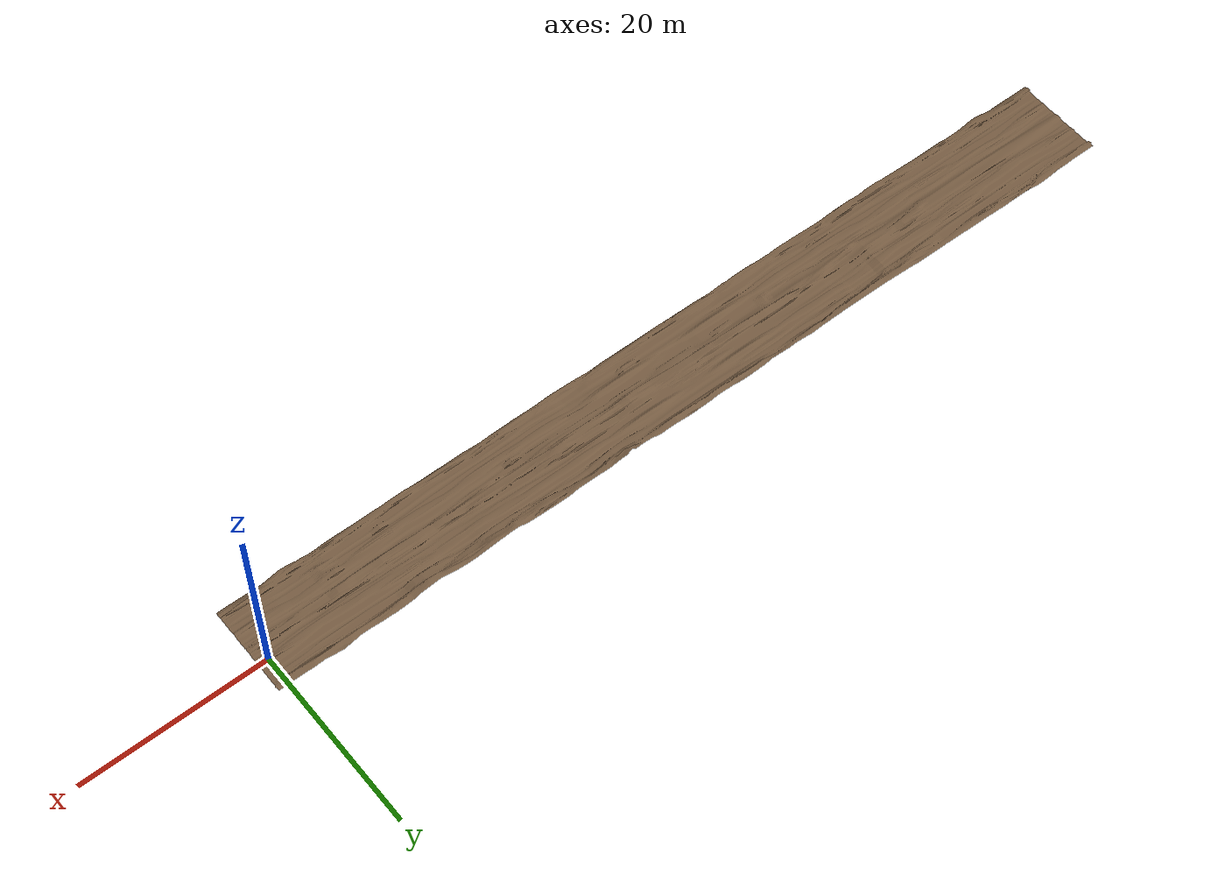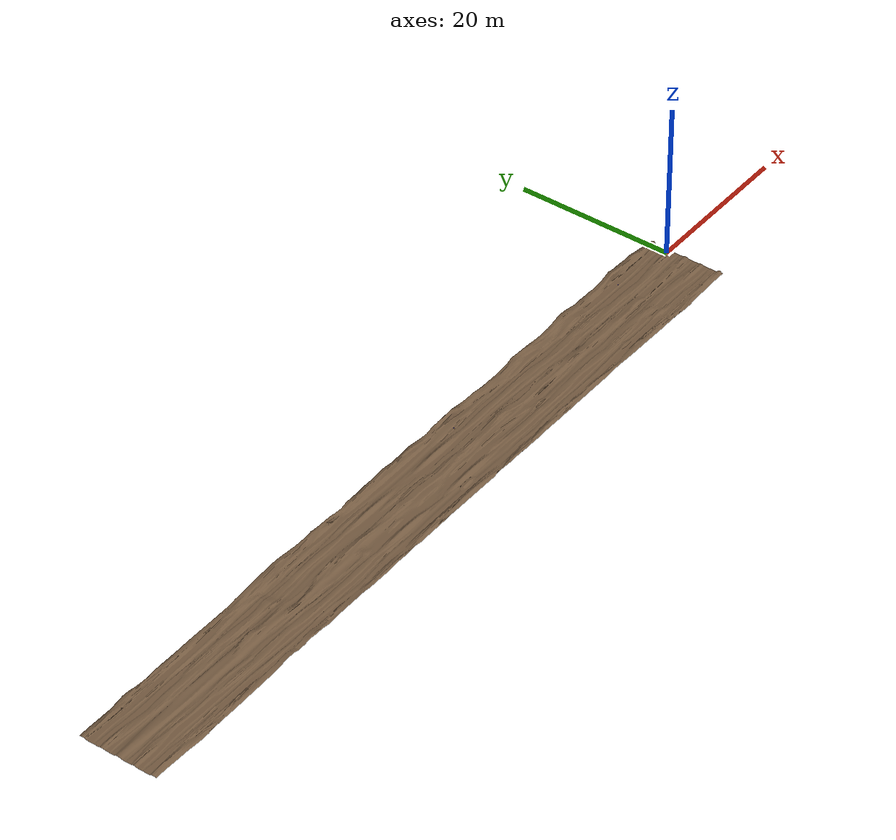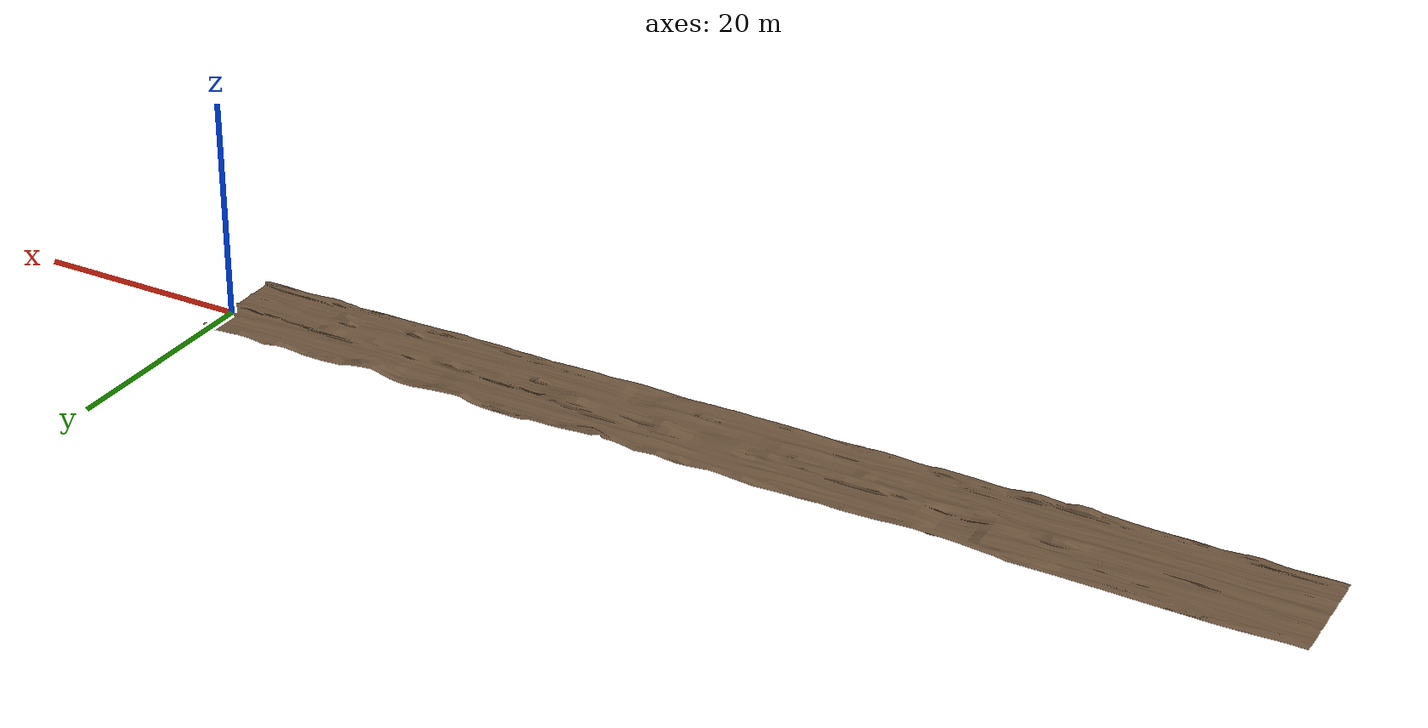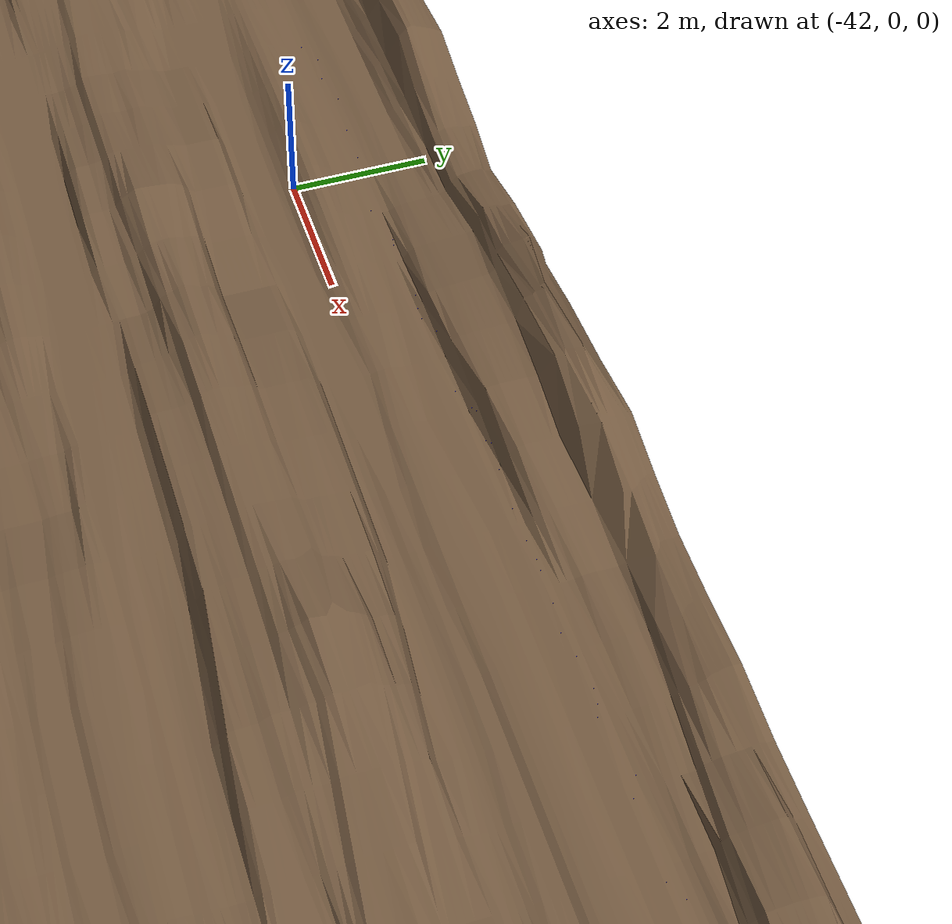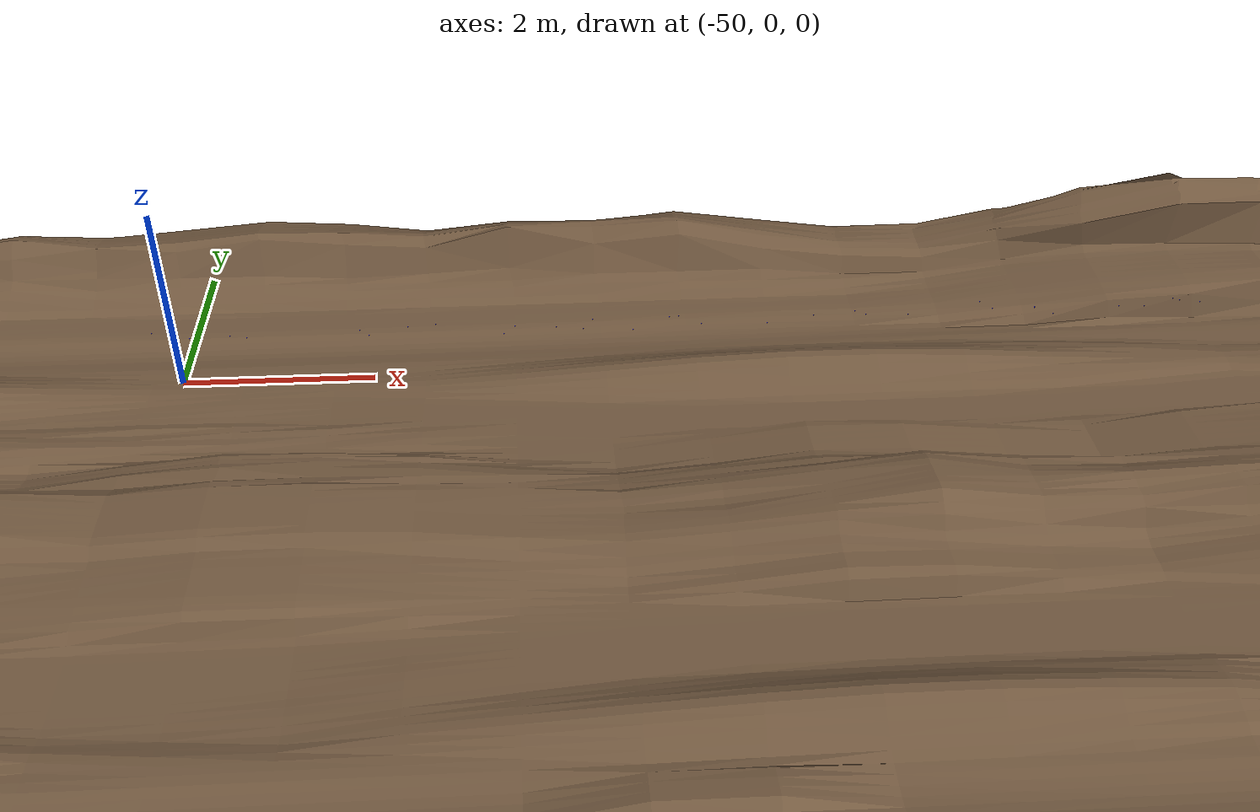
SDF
<sdf version='1.9'>
  <world name='empty'>
    <physics name='1ms' type='ode'>
      <max_step_size>0.001</max_step_size>
      <real_time_factor>1</real_time_factor>
      <real_time_update_rate>1000</real_time_update_rate>
    </physics>
    <plugin name='gz::sim::systems::Physics' filename='ignition-gazebo-physics-system'/>
    <plugin name='gz::sim::systems::UserCommands' filename='ignition-gazebo-user-commands-system'/>
    <plugin name='gz::sim::systems::SceneBroadcaster' filename='ignition-gazebo-scene-broadcaster-system'/>
    <plugin name='gz::sim::systems::Contact' filename='ignition-gazebo-contact-system'/>

    <plugin name='ignition::gazebo::systems::Sensors' filename='ignition-gazebo-sensors-system'/>

    <gravity>0 0 -9.8</gravity>
    <gravity>0 0 -9.8</gravity>
    <magnetic_field>6e-06 2.3e-05 -4.2e-05</magnetic_field>
    <atmosphere type='adiabatic'/>
    <scene>
      <ambient>0.4 0.4 0.4 1</ambient>
      <background>0.7 0.7 0.7 1</background>
      <shadows>true</shadows>
    </scene>

    <!--  Vineyard heightmap terrain (50m x 50m, ~0.5m height span) -->
    <!--  Put vineyard_heightmap.png next to this world file, or   -->

    <model name="vineyard_mesh_inline">
    <static>true</static>
    <!-- x  y   z    R    P      Y(=90deg) -->
    <pose>-49 -2 -0.4 0 0 0</pose>
    <link name="terrain">
      <collision name="col">
        <geometry>
          <mesh>
            <uri>file:///home/alex/.ignition/gazebo/models/vineyard_mesh/meshes/terrain.dae</uri>
            <scale>1 1 1</scale>
          </mesh>
        </geometry>
      </collision>
      <visual name="vis">
        <geometry>
          <mesh>
            <uri>file:///home/alex/.ignition/gazebo/models/vineyard_mesh/meshes/terrain.dae</uri>
            <scale>1 1 1</scale>
          </mesh>
        </geometry>
        <material>
          <ambient>0.4 0.3 0.2 1</ambient>
          <diffuse>0.45 0.35 0.25 1</diffuse>
          <specular>0.1 0.1 0.1 1</specular>
        </material>
      </visual>
    </link>
  </model>

<!-- ROW 1 BLUE TARGETS: 150 spheres (r=0.005), min_dx=0.050m, post_keepout=0.085m, occlusion_x_band=0.120m -->
<model name='row1_target_001'>
  <static>true</static>
  <pose>-50.572 1.121 -0.111 0 0 0</pose>
  <link name='link'>
    <collision name='collision'>
      <geometry><sphere><radius>0.005</radius></sphere></geometry>
    </collision>
    <visual name='visual'>
      <geometry><sphere><radius>0.005</radius></sphere></geometry>
      <material>
        <diffuse>0 0 0.9 1</diffuse>
        <ambient>0 0 0.6 1</ambient>
      </material>
    </visual>
  </link>
</model>
<model name='row1_target_002'>
  <static>true</static>
  <pose>-50.157 1.069 -0.159 0 0 0</pose>
  <link name='link'>
    <collision name='collision'>
      <geometry><sphere><radius>0.005</radius></sphere></geometry>
    </collision>
    <visual name='visual'>
      <geometry><sphere><radius>0.005</radius></sphere></geometry>
      <material>
        <diffuse>0 0 0.9 1</diffuse>
        <ambient>0 0 0.6 1</ambient>
      </material>
    </visual>
  </link>
</model>
<model name='row1_target_003'>
  <static>true</static>
  <pose>-50.453 1.006 -0.145 0 0 0</pose>
  <link name='link'>
    <collision name='collision'>
      <geometry><sphere><radius>0.005</radius></sphere></geometry>
    </collision>
    <visual name='visual'>
      <geometry><sphere><radius>0.005</radius></sphere></geometry>
      <material>
        <diffuse>0 0 0.9 1</diffuse>
        <ambient>0 0 0.6 1</ambient>
      </material>
    </visual>
  </link>
</model>
<model name='row1_target_004'>
  <static>true</static>
  <pose>-49.251 1.214 -0.129 0 0 0</pose>
  <link name='link'>
    <collision name='collision'>
      <geometry><sphere><radius>0.005</radius></sphere></geometry>
    </collision>
    <visual name='visual'>
      <geometry><sphere><radius>0.005</radius></sphere></geometry>
      <material>
        <diffuse>0 0 0.9 1</diffuse>
        <ambient>0 0 0.6 1</ambient>
      </material>
    </visual>
  </link>
</model>
<model name='row1_target_005'>
  <static>true</static>
  <pose>-49.699 1.032 -0.118 0 0 0</pose>
  <link name='link'>
    <collision name='collision'>
      <geometry><sphere><radius>0.005</radius></sphere></geometry>
    </collision>
    <visual name='visual'>
      <geometry><sphere><radius>0.005</radius></sphere></geometry>
      <material>
        <diffuse>0 0 0.9 1</diffuse>
        <ambient>0 0 0.6 1</ambient>
      </material>
    </visual>
  </link>
</model>
<model name='row1_target_006'>
  <static>true</static>
  <pose>-49.524 1.055 -0.167 0 0 0</pose>
  <link name='link'>
    <collision name='collision'>
      <geometry><sphere><radius>0.005</radius></sphere></geometry>
    </collision>
    <visual name='visual'>
      <geometry><sphere><radius>0.005</radius></sphere></geometry>
      <material>
        <diffuse>0 0 0.9 1</diffuse>
        <ambient>0 0 0.6 1</ambient>
      </material>
    </visual>
  </link>
</model>
<model name='row1_target_007'>
  <static>true</static>
  <pose>-48.274 1.114 -0.153 0 0 0</pose>
  <link name='link'>
    <collision name='collision'>
      <geometry><sphere><radius>0.005</radius></sphere></geometry>
    </collision>
    <visual name='visual'>
      <geometry><sphere><radius>0.005</radius></sphere></geometry>
      <material>
        <diffuse>0 0 0.9 1</diffuse>
        <ambient>0 0 0.6 1</ambient>
      </material>
    </visual>
  </link>
</model>
<model name='row1_target_008'>
  <static>true</static>
  <pose>-48.171 1.076 -0.197 0 0 0</pose>
  <link name='link'>
    <collision name='collision'>
      <geometry><sphere><radius>0.005</radius></sphere></geometry>
    </collision>
    <visual name='visual'>
      <geometry><sphere><radius>0.005</radius></sphere></geometry>
      <material>
        <diffuse>0 0 0.9 1</diffuse>
        <ambient>0 0 0.6 1</ambient>
      </material>
    </visual>
  </link>
</model>
<model name='row1_target_009'>
  <static>true</static>
  <pose>-48.749 1.198 -0.112 0 0 0</pose>
  <link name='link'>
    <collision name='collision'>
      <geometry><sphere><radius>0.005</radius></sphere></geometry>
    </collision>
    <visual name='visual'>
      <geometry><sphere><radius>0.005</radius></sphere></geometry>
      <material>
        <diffuse>0 0 0.9 1</diffuse>
        <ambient>0 0 0.6 1</ambient>
      </material>
    </visual>
  </link>
</model>
<model name='row1_target_010'>
  <static>true</static>
  <pose>-47.420 1.193 -0.152 0 0 0</pose>
  <link name='link'>
    <collision name='collision'>
      <geometry><sphere><radius>0.005</radius></sphere></geometry>
    </collision>
    <visual name='visual'>
      <geometry><sphere><radius>0.005</radius></sphere></geometry>
      <material>
        <diffuse>0 0 0.9 1</diffuse>
        <ambient>0 0 0.6 1</ambient>
      </material>
    </visual>
  </link>
</model>
<model name='row1_target_011'>
  <static>true</static>
  <pose>-47.731 1.105 -0.124 0 0 0</pose>
  <link name='link'>
    <collision name='collision'>
      <geometry><sphere><radius>0.005</radius></sphere></geometry>
    </collision>
    <visual name='visual'>
      <geometry><sphere><radius>0.005</radius></sphere></geometry>
      <material>
        <diffuse>0 0 0.9 1</diffuse>
        <ambient>0 0 0.6 1</ambient>
      </material>
    </visual>
  </link>
</model>
<model name='row1_target_012'>
  <static>true</static>
  <pose>-47.859 1.240 -0.165 0 0 0</pose>
  <link name='link'>
    <collision name='collision'>
      <geometry><sphere><radius>0.005</radius></sphere></geometry>
    </collision>
    <visual name='visual'>
      <geometry><sphere><radius>0.005</radius></sphere></geometry>
      <material>
        <diffuse>0 0 0.9 1</diffuse>
        <ambient>0 0 0.6 1</ambient>
      </material>
    </visual>
  </link>
</model>
<model name='row1_target_013'>
  <static>true</static>
  <pose>-46.064 1.026 -0.125 0 0 0</pose>
  <link name='link'>
    <collision name='collision'>
      <geometry><sphere><radius>0.005</radius></sphere></geometry>
    </collision>
    <visual name='visual'>
      <geometry><sphere><radius>0.005</radius></sphere></geometry>
      <material>
        <diffuse>0 0 0.9 1</diffuse>
        <ambient>0 0 0.6 1</ambient>
      </material>
    </visual>
  </link>
</model>
<model name='row1_target_014'>
  <static>true</static>
  <pose>-46.530 1.093 -0.148 0 0 0</pose>
  <link name='link'>
    <collision name='collision'>
      <geometry><sphere><radius>0.005</radius></sphere></geometry>
    </collision>
    <visual name='visual'>
      <geometry><sphere><radius>0.005</radius></sphere></geometry>
      <material>
        <diffuse>0 0 0.9 1</diffuse>
        <ambient>0 0 0.6 1</ambient>
      </material>
    </visual>
  </link>
</model>
<model name='row1_target_015'>
  <static>true</static>
  <pose>-46.653 0.994 -0.176 0 0 0</pose>
  <link name='link'>
    <collision name='collision'>
      <geometry><sphere><radius>0.005</radius></sphere></geometry>
    </collision>
    <visual name='visual'>
      <geometry><sphere><radius>0.005</radius></sphere></geometry>
      <material>
        <diffuse>0 0 0.9 1</diffuse>
        <ambient>0 0 0.6 1</ambient>
      </material>
    </visual>
  </link>
</model>
<model name='row1_target_016'>
  <static>true</static>
  <pose>-45.650 1.162 -0.130 0 0 0</pose>
  <link name='link'>
    <collision name='collision'>
      <geometry><sphere><radius>0.005</radius></sphere></geometry>
    </collision>
    <visual name='visual'>
      <geometry><sphere><radius>0.005</radius></sphere></geometry>
      <material>
        <diffuse>0 0 0.9 1</diffuse>
        <ambient>0 0 0.6 1</ambient>
      </material>
    </visual>
  </link>
</model>
<model name='row1_target_017'>
  <static>true</static>
  <pose>-45.200 0.998 -0.182 0 0 0</pose>
  <link name='link'>
    <collision name='collision'>
      <geometry><sphere><radius>0.005</radius></sphere></geometry>
    </collision>
    <visual name='visual'>
      <geometry><sphere><radius>0.005</radius></sphere></geometry>
      <material>
        <diffuse>0 0 0.9 1</diffuse>
        <ambient>0 0 0.6 1</ambient>
      </material>
    </visual>
  </link>
</model>
<model name='row1_target_018'>
  <static>true</static>
  <pose>-45.756 1.040 -0.171 0 0 0</pose>
  <link name='link'>
    <collision name='collision'>
      <geometry><sphere><radius>0.005</radius></sphere></geometry>
    </collision>
    <visual name='visual'>
      <geometry><sphere><radius>0.005</radius></sphere></geometry>
      <material>
        <diffuse>0 0 0.9 1</diffuse>
        <ambient>0 0 0.6 1</ambient>
      </material>
    </visual>
  </link>
</model>
<model name='row1_target_019'>
  <static>true</static>
  <pose>-44.777 1.153 -0.126 0 0 0</pose>
  <link name='link'>
    <collision name='collision'>
      <geometry><sphere><radius>0.005</radius></sphere></geometry>
    </collision>
    <visual name='visual'>
      <geometry><sphere><radius>0.005</radius></sphere></geometry>
      <material>
        <diffuse>0 0 0.9 1</diffuse>
        <ambient>0 0 0.6 1</ambient>
      </material>
    </visual>
  </link>
</model>
<model name='row1_target_020'>
  <static>true</static>
  <pose>-44.661 1.198 -0.149 0 0 0</pose>
  <link name='link'>
    <collision name='collision'>
      <geometry><sphere><radius>0.005</radius></sphere></geometry>
    </collision>
    <visual name='visual'>
      <geometry><sphere><radius>0.005</radius></sphere></geometry>
      <material>
        <diffuse>0 0 0.9 1</diffuse>
        <ambient>0 0 0.6 1</ambient>
      </material>
    </visual>
  </link>
</model>
<model name='row1_target_021'>
  <static>true</static>
  <pose>-44.412 1.106 -0.198 0 0 0</pose>
  <link name='link'>
    <collision name='collision'>
      <geometry><sphere><radius>0.005</radius></sphere></geometry>
    </collision>
    <visual name='visual'>
      <geometry><sphere><radius>0.005</radius></sphere></geometry>
      <material>
        <diffuse>0 0 0.9 1</diffuse>
        <ambient>0 0 0.6 1</ambient>
      </material>
    </visual>
  </link>
</model>
<model name='row1_target_022'>
  <static>true</static>
  <pose>-43.678 0.992 -0.142 0 0 0</pose>
  <link name='link'>
    <collision name='collision'>
      <geometry><sphere><radius>0.005</radius></sphere></geometry>
    </collision>
    <visual name='visual'>
      <geometry><sphere><radius>0.005</radius></sphere></geometry>
      <material>
        <diffuse>0 0 0.9 1</diffuse>
        <ambient>0 0 0.6 1</ambient>
      </material>
    </visual>
  </link>
</model>
<model name='row1_target_023'>
  <static>true</static>
  <pose>-43.123 1.131 -0.146 0 0 0</pose>
  <link name='link'>
    <collision name='collision'>
      <geometry><sphere><radius>0.005</radius></sphere></geometry>
    </collision>
    <visual name='visual'>
      <geometry><sphere><radius>0.005</radius></sphere></geometry>
      <material>
        <diffuse>0 0 0.9 1</diffuse>
        <ambient>0 0 0.6 1</ambient>
      </material>
    </visual>
  </link>
</model>
<model name='row1_target_024'>
  <static>true</static>
  <pose>-43.845 1.204 -0.153 0 0 0</pose>
  <link name='link'>
    <collision name='collision'>
      <geometry><sphere><radius>0.005</radius></sphere></geometry>
    </collision>
    <visual name='visual'>
      <geometry><sphere><radius>0.005</radius></sphere></geometry>
      <material>
        <diffuse>0 0 0.9 1</diffuse>
        <ambient>0 0 0.6 1</ambient>
      </material>
    </visual>
  </link>
</model>
<model name='row1_target_025'>
  <static>true</static>
  <pose>-42.060 1.031 -0.108 0 0 0</pose>
  <link name='link'>
    <collision name='collision'>
      <geometry><sphere><radius>0.005</radius></sphere></geometry>
    </collision>
    <visual name='visual'>
      <geometry><sphere><radius>0.005</radius></sphere></geometry>
      <material>
        <diffuse>0 0 0.9 1</diffuse>
        <ambient>0 0 0.6 1</ambient>
      </material>
    </visual>
  </link>
</model>
<model name='row1_target_026'>
  <static>true</static>
  <pose>-42.647 1.143 -0.117 0 0 0</pose>
  <link name='link'>
    <collision name='collision'>
      <geometry><sphere><radius>0.005</radius></sphere></geometry>
    </collision>
    <visual name='visual'>
      <geometry><sphere><radius>0.005</radius></sphere></geometry>
      <material>
        <diffuse>0 0 0.9 1</diffuse>
        <ambient>0 0 0.6 1</ambient>
      </material>
    </visual>
  </link>
</model>
<model name='row1_target_027'>
  <static>true</static>
  <pose>-42.517 1.127 -0.160 0 0 0</pose>
  <link name='link'>
    <collision name='collision'>
      <geometry><sphere><radius>0.005</radius></sphere></geometry>
    </collision>
    <visual name='visual'>
      <geometry><sphere><radius>0.005</radius></sphere></geometry>
      <material>
        <diffuse>0 0 0.9 1</diffuse>
        <ambient>0 0 0.6 1</ambient>
      </material>
    </visual>
  </link>
</model>
<model name='row1_target_028'>
  <static>true</static>
  <pose>-41.412 0.997 -0.179 0 0 0</pose>
  <link name='link'>
    <collision name='collision'>
      <geometry><sphere><radius>0.005</radius></sphere></geometry>
    </collision>
    <visual name='visual'>
      <geometry><sphere><radius>0.005</radius></sphere></geometry>
      <material>
        <diffuse>0 0 0.9 1</diffuse>
        <ambient>0 0 0.6 1</ambient>
      </material>
    </visual>
  </link>
</model>
<model name='row1_target_029'>
  <static>true</static>
  <pose>-41.180 1.237 -0.105 0 0 0</pose>
  <link name='link'>
    <collision name='collision'>
      <geometry><sphere><radius>0.005</radius></sphere></geometry>
    </collision>
    <visual name='visual'>
      <geometry><sphere><radius>0.005</radius></sphere></geometry>
      <material>
        <diffuse>0 0 0.9 1</diffuse>
        <ambient>0 0 0.6 1</ambient>
      </material>
    </visual>
  </link>
</model>
<model name='row1_target_030'>
  <static>true</static>
  <pose>-41.041 1.158 -0.155 0 0 0</pose>
  <link name='link'>
    <collision name='collision'>
      <geometry><sphere><radius>0.005</radius></sphere></geometry>
    </collision>
    <visual name='visual'>
      <geometry><sphere><radius>0.005</radius></sphere></geometry>
      <material>
        <diffuse>0 0 0.9 1</diffuse>
        <ambient>0 0 0.6 1</ambient>
      </material>
    </visual>
  </link>
</model>
<model name='row1_target_031'>
  <static>true</static>
  <pose>-40.367 1.042 -0.166 0 0 0</pose>
  <link name='link'>
    <collision name='collision'>
      <geometry><sphere><radius>0.005</radius></sphere></geometry>
    </collision>
    <visual name='visual'>
      <geometry><sphere><radius>0.005</radius></sphere></geometry>
      <material>
        <diffuse>0 0 0.9 1</diffuse>
        <ambient>0 0 0.6 1</ambient>
      </material>
    </visual>
  </link>
</model>
<model name='row1_target_032'>
  <static>true</static>
  <pose>-40.750 1.124 -0.168 0 0 0</pose>
  <link name='link'>
    <collision name='collision'>
      <geometry><sphere><radius>0.005</radius></sphere></geometry>
    </collision>
    <visual name='visual'>
      <geometry><sphere><radius>0.005</radius></sphere></geometry>
      <material>
        <diffuse>0 0 0.9 1</diffuse>
        <ambient>0 0 0.6 1</ambient>
      </material>
    </visual>
  </link>
</model>
<model name='row1_target_033'>
  <static>true</static>
  <pose>-40.584 1.081 -0.102 0 0 0</pose>
  <link name='link'>
    <collision name='collision'>
      <geometry><sphere><radius>0.005</radius></sphere></geometry>
    </collision>
    <visual name='visual'>
      <geometry><sphere><radius>0.005</radius></sphere></geometry>
      <material>
        <diffuse>0 0 0.9 1</diffuse>
        <ambient>0 0 0.6 1</ambient>
      </material>
    </visual>
  </link>
</model>
<model name='row1_target_034'>
  <static>true</static>
  <pose>-39.211 1.062 -0.199 0 0 0</pose>
  <link name='link'>
    <collision name='collision'>
      <geometry><sphere><radius>0.005</radius></sphere></geometry>
    </collision>
    <visual name='visual'>
      <geometry><sphere><radius>0.005</radius></sphere></geometry>
      <material>
        <diffuse>0 0 0.9 1</diffuse>
        <ambient>0 0 0.6 1</ambient>
      </material>
    </visual>
  </link>
</model>
<model name='row1_target_035'>
  <static>true</static>
  <pose>-39.588 1.094 -0.130 0 0 0</pose>
  <link name='link'>
    <collision name='collision'>
      <geometry><sphere><radius>0.005</radius></sphere></geometry>
    </collision>
    <visual name='visual'>
      <geometry><sphere><radius>0.005</radius></sphere></geometry>
      <material>
        <diffuse>0 0 0.9 1</diffuse>
        <ambient>0 0 0.6 1</ambient>
      </material>
    </visual>
  </link>
</model>
<model name='row1_target_036'>
  <static>true</static>
  <pose>-39.318 1.033 -0.101 0 0 0</pose>
  <link name='link'>
    <collision name='collision'>
      <geometry><sphere><radius>0.005</radius></sphere></geometry>
    </collision>
    <visual name='visual'>
      <geometry><sphere><radius>0.005</radius></sphere></geometry>
      <material>
        <diffuse>0 0 0.9 1</diffuse>
        <ambient>0 0 0.6 1</ambient>
      </material>
    </visual>
  </link>
</model>
<model name='row1_target_037'>
  <static>true</static>
  <pose>-38.630 1.115 -0.126 0 0 0</pose>
  <link name='link'>
    <collision name='collision'>
      <geometry><sphere><radius>0.005</radius></sphere></geometry>
    </collision>
    <visual name='visual'>
      <geometry><sphere><radius>0.005</radius></sphere></geometry>
      <material>
        <diffuse>0 0 0.9 1</diffuse>
        <ambient>0 0 0.6 1</ambient>
      </material>
    </visual>
  </link>
</model>
<model name='row1_target_038'>
  <static>true</static>
  <pose>-38.905 1.212 -0.129 0 0 0</pose>
  <link name='link'>
    <collision name='collision'>
      <geometry><sphere><radius>0.005</radius></sphere></geometry>
    </collision>
    <visual name='visual'>
      <geometry><sphere><radius>0.005</radius></sphere></geometry>
      <material>
        <diffuse>0 0 0.9 1</diffuse>
        <ambient>0 0 0.6 1</ambient>
      </material>
    </visual>
  </link>
</model>
<model name='row1_target_039'>
  <static>true</static>
  <pose>-38.853 1.156 -0.116 0 0 0</pose>
  <link name='link'>
    <collision name='collision'>
      <geometry><sphere><radius>0.005</radius></sphere></geometry>
    </collision>
    <visual name='visual'>
      <geometry><sphere><radius>0.005</radius></sphere></geometry>
      <material>
        <diffuse>0 0 0.9 1</diffuse>
        <ambient>0 0 0.6 1</ambient>
      </material>
    </visual>
  </link>
</model>
<model name='row1_target_040'>
  <static>true</static>
  <pose>-37.460 1.197 -0.158 0 0 0</pose>
  <link name='link'>
    <collision name='collision'>
      <geometry><sphere><radius>0.005</radius></sphere></geometry>
    </collision>
    <visual name='visual'>
      <geometry><sphere><radius>0.005</radius></sphere></geometry>
      <material>
        <diffuse>0 0 0.9 1</diffuse>
        <ambient>0 0 0.6 1</ambient>
      </material>
    </visual>
  </link>
</model>
<model name='row1_target_041'>
  <static>true</static>
  <pose>-37.814 1.086 -0.191 0 0 0</pose>
  <link name='link'>
    <collision name='collision'>
      <geometry><sphere><radius>0.005</radius></sphere></geometry>
    </collision>
    <visual name='visual'>
      <geometry><sphere><radius>0.005</radius></sphere></geometry>
      <material>
        <diffuse>0 0 0.9 1</diffuse>
        <ambient>0 0 0.6 1</ambient>
      </material>
    </visual>
  </link>
</model>
<model name='row1_target_042'>
  <static>true</static>
  <pose>-37.378 1.232 -0.134 0 0 0</pose>
  <link name='link'>
    <collision name='collision'>
      <geometry><sphere><radius>0.005</radius></sphere></geometry>
    </collision>
    <visual name='visual'>
      <geometry><sphere><radius>0.005</radius></sphere></geometry>
      <material>
        <diffuse>0 0 0.9 1</diffuse>
        <ambient>0 0 0.6 1</ambient>
      </material>
    </visual>
  </link>
</model>
<model name='row1_target_043'>
  <static>true</static>
  <pose>-36.873 1.195 -0.149 0 0 0</pose>
  <link name='link'>
    <collision name='collision'>
      <geometry><sphere><radius>0.005</radius></sphere></geometry>
    </collision>
    <visual name='visual'>
      <geometry><sphere><radius>0.005</radius></sphere></geometry>
      <material>
        <diffuse>0 0 0.9 1</diffuse>
        <ambient>0 0 0.6 1</ambient>
      </material>
    </visual>
  </link>
</model>
<model name='row1_target_044'>
  <static>true</static>
  <pose>-36.776 1.234 -0.102 0 0 0</pose>
  <link name='link'>
    <collision name='collision'>
      <geometry><sphere><radius>0.005</radius></sphere></geometry>
    </collision>
    <visual name='visual'>
      <geometry><sphere><radius>0.005</radius></sphere></geometry>
      <material>
        <diffuse>0 0 0.9 1</diffuse>
        <ambient>0 0 0.6 1</ambient>
      </material>
    </visual>
  </link>
</model>
<model name='row1_target_045'>
  <static>true</static>
  <pose>-36.365 1.203 -0.145 0 0 0</pose>
  <link name='link'>
    <collision name='collision'>
      <geometry><sphere><radius>0.005</radius></sphere></geometry>
    </collision>
    <visual name='visual'>
      <geometry><sphere><radius>0.005</radius></sphere></geometry>
      <material>
        <diffuse>0 0 0.9 1</diffuse>
        <ambient>0 0 0.6 1</ambient>
      </material>
    </visual>
  </link>
</model>
<model name='row1_target_046'>
  <static>true</static>
  <pose>-35.222 1.170 -0.185 0 0 0</pose>
  <link name='link'>
    <collision name='collision'>
      <geometry><sphere><radius>0.005</radius></sphere></geometry>
    </collision>
    <visual name='visual'>
      <geometry><sphere><radius>0.005</radius></sphere></geometry>
      <material>
        <diffuse>0 0 0.9 1</diffuse>
        <ambient>0 0 0.6 1</ambient>
      </material>
    </visual>
  </link>
</model>
<model name='row1_target_047'>
  <static>true</static>
  <pose>-35.697 1.146 -0.103 0 0 0</pose>
  <link name='link'>
    <collision name='collision'>
      <geometry><sphere><radius>0.005</radius></sphere></geometry>
    </collision>
    <visual name='visual'>
      <geometry><sphere><radius>0.005</radius></sphere></geometry>
      <material>
        <diffuse>0 0 0.9 1</diffuse>
        <ambient>0 0 0.6 1</ambient>
      </material>
    </visual>
  </link>
</model>
<model name='row1_target_048'>
  <static>true</static>
  <pose>-35.796 1.112 -0.149 0 0 0</pose>
  <link name='link'>
    <collision name='collision'>
      <geometry><sphere><radius>0.005</radius></sphere></geometry>
    </collision>
    <visual name='visual'>
      <geometry><sphere><radius>0.005</radius></sphere></geometry>
      <material>
        <diffuse>0 0 0.9 1</diffuse>
        <ambient>0 0 0.6 1</ambient>
      </material>
    </visual>
  </link>
</model>
<model name='row1_target_049'>
  <static>true</static>
  <pose>-34.245 1.161 -0.184 0 0 0</pose>
  <link name='link'>
    <collision name='collision'>
      <geometry><sphere><radius>0.005</radius></sphere></geometry>
    </collision>
    <visual name='visual'>
      <geometry><sphere><radius>0.005</radius></sphere></geometry>
      <material>
        <diffuse>0 0 0.9 1</diffuse>
        <ambient>0 0 0.6 1</ambient>
      </material>
    </visual>
  </link>
</model>
<model name='row1_target_050'>
  <static>true</static>
  <pose>-34.879 1.177 -0.131 0 0 0</pose>
  <link name='link'>
    <collision name='collision'>
      <geometry><sphere><radius>0.005</radius></sphere></geometry>
    </collision>
    <visual name='visual'>
      <geometry><sphere><radius>0.005</radius></sphere></geometry>
      <material>
        <diffuse>0 0 0.9 1</diffuse>
        <ambient>0 0 0.6 1</ambient>
      </material>
    </visual>
  </link>
</model>
<model name='row1_target_051'>
  <static>true</static>
  <pose>-34.739 1.177 -0.170 0 0 0</pose>
  <link name='link'>
    <collision name='collision'>
      <geometry><sphere><radius>0.005</radius></sphere></geometry>
    </collision>
    <visual name='visual'>
      <geometry><sphere><radius>0.005</radius></sphere></geometry>
      <material>
        <diffuse>0 0 0.9 1</diffuse>
        <ambient>0 0 0.6 1</ambient>
      </material>
    </visual>
  </link>
</model>
<model name='row1_target_052'>
  <static>true</static>
  <pose>-33.423 1.152 -0.153 0 0 0</pose>
  <link name='link'>
    <collision name='collision'>
      <geometry><sphere><radius>0.005</radius></sphere></geometry>
    </collision>
    <visual name='visual'>
      <geometry><sphere><radius>0.005</radius></sphere></geometry>
      <material>
        <diffuse>0 0 0.9 1</diffuse>
        <ambient>0 0 0.6 1</ambient>
      </material>
    </visual>
  </link>
</model>
<model name='row1_target_053'>
  <static>true</static>
  <pose>-33.174 1.131 -0.198 0 0 0</pose>
  <link name='link'>
    <collision name='collision'>
      <geometry><sphere><radius>0.005</radius></sphere></geometry>
    </collision>
    <visual name='visual'>
      <geometry><sphere><radius>0.005</radius></sphere></geometry>
      <material>
        <diffuse>0 0 0.9 1</diffuse>
        <ambient>0 0 0.6 1</ambient>
      </material>
    </visual>
  </link>
</model>
<model name='row1_target_054'>
  <static>true</static>
  <pose>-33.793 1.091 -0.154 0 0 0</pose>
  <link name='link'>
    <collision name='collision'>
      <geometry><sphere><radius>0.005</radius></sphere></geometry>
    </collision>
    <visual name='visual'>
      <geometry><sphere><radius>0.005</radius></sphere></geometry>
      <material>
        <diffuse>0 0 0.9 1</diffuse>
        <ambient>0 0 0.6 1</ambient>
      </material>
    </visual>
  </link>
</model>
<model name='row1_target_055'>
  <static>true</static>
  <pose>-32.744 1.171 -0.182 0 0 0</pose>
  <link name='link'>
    <collision name='collision'>
      <geometry><sphere><radius>0.005</radius></sphere></geometry>
    </collision>
    <visual name='visual'>
      <geometry><sphere><radius>0.005</radius></sphere></geometry>
      <material>
        <diffuse>0 0 0.9 1</diffuse>
        <ambient>0 0 0.6 1</ambient>
      </material>
    </visual>
  </link>
</model>
<model name='row1_target_056'>
  <static>true</static>
  <pose>-32.583 1.107 -0.190 0 0 0</pose>
  <link name='link'>
    <collision name='collision'>
      <geometry><sphere><radius>0.005</radius></sphere></geometry>
    </collision>
    <visual name='visual'>
      <geometry><sphere><radius>0.005</radius></sphere></geometry>
      <material>
        <diffuse>0 0 0.9 1</diffuse>
        <ambient>0 0 0.6 1</ambient>
      </material>
    </visual>
  </link>
</model>
<model name='row1_target_057'>
  <static>true</static>
  <pose>-32.949 1.201 -0.171 0 0 0</pose>
  <link name='link'>
    <collision name='collision'>
      <geometry><sphere><radius>0.005</radius></sphere></geometry>
    </collision>
    <visual name='visual'>
      <geometry><sphere><radius>0.005</radius></sphere></geometry>
      <material>
        <diffuse>0 0 0.9 1</diffuse>
        <ambient>0 0 0.6 1</ambient>
      </material>
    </visual>
  </link>
</model>
<model name='row1_target_058'>
  <static>true</static>
  <pose>-31.857 1.122 -0.193 0 0 0</pose>
  <link name='link'>
    <collision name='collision'>
      <geometry><sphere><radius>0.005</radius></sphere></geometry>
    </collision>
    <visual name='visual'>
      <geometry><sphere><radius>0.005</radius></sphere></geometry>
      <material>
        <diffuse>0 0 0.9 1</diffuse>
        <ambient>0 0 0.6 1</ambient>
      </material>
    </visual>
  </link>
</model>
<model name='row1_target_059'>
  <static>true</static>
  <pose>-31.717 1.236 -0.142 0 0 0</pose>
  <link name='link'>
    <collision name='collision'>
      <geometry><sphere><radius>0.005</radius></sphere></geometry>
    </collision>
    <visual name='visual'>
      <geometry><sphere><radius>0.005</radius></sphere></geometry>
      <material>
        <diffuse>0 0 0.9 1</diffuse>
        <ambient>0 0 0.6 1</ambient>
      </material>
    </visual>
  </link>
</model>
<model name='row1_target_060'>
  <static>true</static>
  <pose>-31.431 1.095 -0.123 0 0 0</pose>
  <link name='link'>
    <collision name='collision'>
      <geometry><sphere><radius>0.005</radius></sphere></geometry>
    </collision>
    <visual name='visual'>
      <geometry><sphere><radius>0.005</radius></sphere></geometry>
      <material>
        <diffuse>0 0 0.9 1</diffuse>
        <ambient>0 0 0.6 1</ambient>
      </material>
    </visual>
  </link>
</model>
<model name='row1_target_061'>
  <static>true</static>
  <pose>-30.131 1.203 -0.150 0 0 0</pose>
  <link name='link'>
    <collision name='collision'>
      <geometry><sphere><radius>0.005</radius></sphere></geometry>
    </collision>
    <visual name='visual'>
      <geometry><sphere><radius>0.005</radius></sphere></geometry>
      <material>
        <diffuse>0 0 0.9 1</diffuse>
        <ambient>0 0 0.6 1</ambient>
      </material>
    </visual>
  </link>
</model>
<model name='row1_target_062'>
  <static>true</static>
  <pose>-30.554 1.000 -0.186 0 0 0</pose>
  <link name='link'>
    <collision name='collision'>
      <geometry><sphere><radius>0.005</radius></sphere></geometry>
    </collision>
    <visual name='visual'>
      <geometry><sphere><radius>0.005</radius></sphere></geometry>
      <material>
        <diffuse>0 0 0.9 1</diffuse>
        <ambient>0 0 0.6 1</ambient>
      </material>
    </visual>
  </link>
</model>
<model name='row1_target_063'>
  <static>true</static>
  <pose>-30.397 1.084 -0.194 0 0 0</pose>
  <link name='link'>
    <collision name='collision'>
      <geometry><sphere><radius>0.005</radius></sphere></geometry>
    </collision>
    <visual name='visual'>
      <geometry><sphere><radius>0.005</radius></sphere></geometry>
      <material>
        <diffuse>0 0 0.9 1</diffuse>
        <ambient>0 0 0.6 1</ambient>
      </material>
    </visual>
  </link>
</model>
<model name='row1_target_064'>
  <static>true</static>
  <pose>-29.163 1.086 -0.128 0 0 0</pose>
  <link name='link'>
    <collision name='collision'>
      <geometry><sphere><radius>0.005</radius></sphere></geometry>
    </collision>
    <visual name='visual'>
      <geometry><sphere><radius>0.005</radius></sphere></geometry>
      <material>
        <diffuse>0 0 0.9 1</diffuse>
        <ambient>0 0 0.6 1</ambient>
      </material>
    </visual>
  </link>
</model>
<model name='row1_target_065'>
  <static>true</static>
  <pose>-29.540 1.040 -0.169 0 0 0</pose>
  <link name='link'>
    <collision name='collision'>
      <geometry><sphere><radius>0.005</radius></sphere></geometry>
    </collision>
    <visual name='visual'>
      <geometry><sphere><radius>0.005</radius></sphere></geometry>
      <material>
        <diffuse>0 0 0.9 1</diffuse>
        <ambient>0 0 0.6 1</ambient>
      </material>
    </visual>
  </link>
</model>
<model name='row1_target_066'>
  <static>true</static>
  <pose>-29.696 1.027 -0.199 0 0 0</pose>
  <link name='link'>
    <collision name='collision'>
      <geometry><sphere><radius>0.005</radius></sphere></geometry>
    </collision>
    <visual name='visual'>
      <geometry><sphere><radius>0.005</radius></sphere></geometry>
      <material>
        <diffuse>0 0 0.9 1</diffuse>
        <ambient>0 0 0.6 1</ambient>
      </material>
    </visual>
  </link>
</model>
<model name='row1_target_067'>
  <static>true</static>
  <pose>-28.128 1.148 -0.107 0 0 0</pose>
  <link name='link'>
    <collision name='collision'>
      <geometry><sphere><radius>0.005</radius></sphere></geometry>
    </collision>
    <visual name='visual'>
      <geometry><sphere><radius>0.005</radius></sphere></geometry>
      <material>
        <diffuse>0 0 0.9 1</diffuse>
        <ambient>0 0 0.6 1</ambient>
      </material>
    </visual>
  </link>
</model>
<model name='row1_target_068'>
  <static>true</static>
  <pose>-28.348 1.043 -0.194 0 0 0</pose>
  <link name='link'>
    <collision name='collision'>
      <geometry><sphere><radius>0.005</radius></sphere></geometry>
    </collision>
    <visual name='visual'>
      <geometry><sphere><radius>0.005</radius></sphere></geometry>
      <material>
        <diffuse>0 0 0.9 1</diffuse>
        <ambient>0 0 0.6 1</ambient>
      </material>
    </visual>
  </link>
</model>
<model name='row1_target_069'>
  <static>true</static>
  <pose>-28.222 1.028 -0.186 0 0 0</pose>
  <link name='link'>
    <collision name='collision'>
      <geometry><sphere><radius>0.005</radius></sphere></geometry>
    </collision>
    <visual name='visual'>
      <geometry><sphere><radius>0.005</radius></sphere></geometry>
      <material>
        <diffuse>0 0 0.9 1</diffuse>
        <ambient>0 0 0.6 1</ambient>
      </material>
    </visual>
  </link>
</model>
<model name='row1_target_070'>
  <static>true</static>
  <pose>-27.023 1.014 -0.150 0 0 0</pose>
  <link name='link'>
    <collision name='collision'>
      <geometry><sphere><radius>0.005</radius></sphere></geometry>
    </collision>
    <visual name='visual'>
      <geometry><sphere><radius>0.005</radius></sphere></geometry>
      <material>
        <diffuse>0 0 0.9 1</diffuse>
        <ambient>0 0 0.6 1</ambient>
      </material>
    </visual>
  </link>
</model>
<model name='row1_target_071'>
  <static>true</static>
  <pose>-27.153 1.028 -0.109 0 0 0</pose>
  <link name='link'>
    <collision name='collision'>
      <geometry><sphere><radius>0.005</radius></sphere></geometry>
    </collision>
    <visual name='visual'>
      <geometry><sphere><radius>0.005</radius></sphere></geometry>
      <material>
        <diffuse>0 0 0.9 1</diffuse>
        <ambient>0 0 0.6 1</ambient>
      </material>
    </visual>
  </link>
</model>
<model name='row1_target_072'>
  <static>true</static>
  <pose>-27.725 1.002 -0.100 0 0 0</pose>
  <link name='link'>
    <collision name='collision'>
      <geometry><sphere><radius>0.005</radius></sphere></geometry>
    </collision>
    <visual name='visual'>
      <geometry><sphere><radius>0.005</radius></sphere></geometry>
      <material>
        <diffuse>0 0 0.9 1</diffuse>
        <ambient>0 0 0.6 1</ambient>
      </material>
    </visual>
  </link>
</model>
<model name='row1_target_073'>
  <static>true</static>
  <pose>-26.888 1.124 -0.199 0 0 0</pose>
  <link name='link'>
    <collision name='collision'>
      <geometry><sphere><radius>0.005</radius></sphere></geometry>
    </collision>
    <visual name='visual'>
      <geometry><sphere><radius>0.005</radius></sphere></geometry>
      <material>
        <diffuse>0 0 0.9 1</diffuse>
        <ambient>0 0 0.6 1</ambient>
      </material>
    </visual>
  </link>
</model>
<model name='row1_target_074'>
  <static>true</static>
  <pose>-26.572 1.127 -0.144 0 0 0</pose>
  <link name='link'>
    <collision name='collision'>
      <geometry><sphere><radius>0.005</radius></sphere></geometry>
    </collision>
    <visual name='visual'>
      <geometry><sphere><radius>0.005</radius></sphere></geometry>
      <material>
        <diffuse>0 0 0.9 1</diffuse>
        <ambient>0 0 0.6 1</ambient>
      </material>
    </visual>
  </link>
</model>
<model name='row1_target_075'>
  <static>true</static>
  <pose>-26.215 1.183 -0.168 0 0 0</pose>
  <link name='link'>
    <collision name='collision'>
      <geometry><sphere><radius>0.005</radius></sphere></geometry>
    </collision>
    <visual name='visual'>
      <geometry><sphere><radius>0.005</radius></sphere></geometry>
      <material>
        <diffuse>0 0 0.9 1</diffuse>
        <ambient>0 0 0.6 1</ambient>
      </material>
    </visual>
  </link>
</model>
<model name='row1_target_076'>
  <static>true</static>
  <pose>-25.849 1.054 -0.159 0 0 0</pose>
  <link name='link'>
    <collision name='collision'>
      <geometry><sphere><radius>0.005</radius></sphere></geometry>
    </collision>
    <visual name='visual'>
      <geometry><sphere><radius>0.005</radius></sphere></geometry>
      <material>
        <diffuse>0 0 0.9 1</diffuse>
        <ambient>0 0 0.6 1</ambient>
      </material>
    </visual>
  </link>
</model>
<model name='row1_target_077'>
  <static>true</static>
  <pose>-25.730 1.205 -0.105 0 0 0</pose>
  <link name='link'>
    <collision name='collision'>
      <geometry><sphere><radius>0.005</radius></sphere></geometry>
    </collision>
    <visual name='visual'>
      <geometry><sphere><radius>0.005</radius></sphere></geometry>
      <material>
        <diffuse>0 0 0.9 1</diffuse>
        <ambient>0 0 0.6 1</ambient>
      </material>
    </visual>
  </link>
</model>
<model name='row1_target_078'>
  <static>true</static>
  <pose>-25.239 0.977 -0.124 0 0 0</pose>
  <link name='link'>
    <collision name='collision'>
      <geometry><sphere><radius>0.005</radius></sphere></geometry>
    </collision>
    <visual name='visual'>
      <geometry><sphere><radius>0.005</radius></sphere></geometry>
      <material>
        <diffuse>0 0 0.9 1</diffuse>
        <ambient>0 0 0.6 1</ambient>
      </material>
    </visual>
  </link>
</model>
<model name='row1_target_079'>
  <static>true</static>
  <pose>-24.336 1.076 -0.148 0 0 0</pose>
  <link name='link'>
    <collision name='collision'>
      <geometry><sphere><radius>0.005</radius></sphere></geometry>
    </collision>
    <visual name='visual'>
      <geometry><sphere><radius>0.005</radius></sphere></geometry>
      <material>
        <diffuse>0 0 0.9 1</diffuse>
        <ambient>0 0 0.6 1</ambient>
      </material>
    </visual>
  </link>
</model>
<model name='row1_target_080'>
  <static>true</static>
  <pose>-24.165 1.000 -0.151 0 0 0</pose>
  <link name='link'>
    <collision name='collision'>
      <geometry><sphere><radius>0.005</radius></sphere></geometry>
    </collision>
    <visual name='visual'>
      <geometry><sphere><radius>0.005</radius></sphere></geometry>
      <material>
        <diffuse>0 0 0.9 1</diffuse>
        <ambient>0 0 0.6 1</ambient>
      </material>
    </visual>
  </link>
</model>
<model name='row1_target_081'>
  <static>true</static>
  <pose>-24.235 1.000 -0.141 0 0 0</pose>
  <link name='link'>
    <collision name='collision'>
      <geometry><sphere><radius>0.005</radius></sphere></geometry>
    </collision>
    <visual name='visual'>
      <geometry><sphere><radius>0.005</radius></sphere></geometry>
      <material>
        <diffuse>0 0 0.9 1</diffuse>
        <ambient>0 0 0.6 1</ambient>
      </material>
    </visual>
  </link>
</model>
<model name='row1_target_082'>
  <static>true</static>
  <pose>-23.330 0.982 -0.116 0 0 0</pose>
  <link name='link'>
    <collision name='collision'>
      <geometry><sphere><radius>0.005</radius></sphere></geometry>
    </collision>
    <visual name='visual'>
      <geometry><sphere><radius>0.005</radius></sphere></geometry>
      <material>
        <diffuse>0 0 0.9 1</diffuse>
        <ambient>0 0 0.6 1</ambient>
      </material>
    </visual>
  </link>
</model>
<model name='row1_target_083'>
  <static>true</static>
  <pose>-23.175 1.073 -0.174 0 0 0</pose>
  <link name='link'>
    <collision name='collision'>
      <geometry><sphere><radius>0.005</radius></sphere></geometry>
    </collision>
    <visual name='visual'>
      <geometry><sphere><radius>0.005</radius></sphere></geometry>
      <material>
        <diffuse>0 0 0.9 1</diffuse>
        <ambient>0 0 0.6 1</ambient>
      </material>
    </visual>
  </link>
</model>
<model name='row1_target_084'>
  <static>true</static>
  <pose>-23.106 1.120 -0.155 0 0 0</pose>
  <link name='link'>
    <collision name='collision'>
      <geometry><sphere><radius>0.005</radius></sphere></geometry>
    </collision>
    <visual name='visual'>
      <geometry><sphere><radius>0.005</radius></sphere></geometry>
      <material>
        <diffuse>0 0 0.9 1</diffuse>
        <ambient>0 0 0.6 1</ambient>
      </material>
    </visual>
  </link>
</model>
<model name='row1_target_085'>
  <static>true</static>
  <pose>-22.262 1.219 -0.185 0 0 0</pose>
  <link name='link'>
    <collision name='collision'>
      <geometry><sphere><radius>0.005</radius></sphere></geometry>
    </collision>
    <visual name='visual'>
      <geometry><sphere><radius>0.005</radius></sphere></geometry>
      <material>
        <diffuse>0 0 0.9 1</diffuse>
        <ambient>0 0 0.6 1</ambient>
      </material>
    </visual>
  </link>
</model>
<model name='row1_target_086'>
  <static>true</static>
  <pose>-22.517 1.110 -0.119 0 0 0</pose>
  <link name='link'>
    <collision name='collision'>
      <geometry><sphere><radius>0.005</radius></sphere></geometry>
    </collision>
    <visual name='visual'>
      <geometry><sphere><radius>0.005</radius></sphere></geometry>
      <material>
        <diffuse>0 0 0.9 1</diffuse>
        <ambient>0 0 0.6 1</ambient>
      </material>
    </visual>
  </link>
</model>
<model name='row1_target_087'>
  <static>true</static>
  <pose>-22.789 1.024 -0.101 0 0 0</pose>
  <link name='link'>
    <collision name='collision'>
      <geometry><sphere><radius>0.005</radius></sphere></geometry>
    </collision>
    <visual name='visual'>
      <geometry><sphere><radius>0.005</radius></sphere></geometry>
      <material>
        <diffuse>0 0 0.9 1</diffuse>
        <ambient>0 0 0.6 1</ambient>
      </material>
    </visual>
  </link>
</model>
<model name='row1_target_088'>
  <static>true</static>
  <pose>-21.441 1.000 -0.189 0 0 0</pose>
  <link name='link'>
    <collision name='collision'>
      <geometry><sphere><radius>0.005</radius></sphere></geometry>
    </collision>
    <visual name='visual'>
      <geometry><sphere><radius>0.005</radius></sphere></geometry>
      <material>
        <diffuse>0 0 0.9 1</diffuse>
        <ambient>0 0 0.6 1</ambient>
      </material>
    </visual>
  </link>
</model>
<model name='row1_target_089'>
  <static>true</static>
  <pose>-21.908 1.075 -0.180 0 0 0</pose>
  <link name='link'>
    <collision name='collision'>
      <geometry><sphere><radius>0.005</radius></sphere></geometry>
    </collision>
    <visual name='visual'>
      <geometry><sphere><radius>0.005</radius></sphere></geometry>
      <material>
        <diffuse>0 0 0.9 1</diffuse>
        <ambient>0 0 0.6 1</ambient>
      </material>
    </visual>
  </link>
</model>
<model name='row1_target_090'>
  <static>true</static>
  <pose>-21.219 1.153 -0.170 0 0 0</pose>
  <link name='link'>
    <collision name='collision'>
      <geometry><sphere><radius>0.005</radius></sphere></geometry>
    </collision>
    <visual name='visual'>
      <geometry><sphere><radius>0.005</radius></sphere></geometry>
      <material>
        <diffuse>0 0 0.9 1</diffuse>
        <ambient>0 0 0.6 1</ambient>
      </material>
    </visual>
  </link>
</model>
<model name='row1_target_091'>
  <static>true</static>
  <pose>-20.452 1.150 -0.112 0 0 0</pose>
  <link name='link'>
    <collision name='collision'>
      <geometry><sphere><radius>0.005</radius></sphere></geometry>
    </collision>
    <visual name='visual'>
      <geometry><sphere><radius>0.005</radius></sphere></geometry>
      <material>
        <diffuse>0 0 0.9 1</diffuse>
        <ambient>0 0 0.6 1</ambient>
      </material>
    </visual>
  </link>
</model>
<model name='row1_target_092'>
  <static>true</static>
  <pose>-20.184 0.974 -0.169 0 0 0</pose>
  <link name='link'>
    <collision name='collision'>
      <geometry><sphere><radius>0.005</radius></sphere></geometry>
    </collision>
    <visual name='visual'>
      <geometry><sphere><radius>0.005</radius></sphere></geometry>
      <material>
        <diffuse>0 0 0.9 1</diffuse>
        <ambient>0 0 0.6 1</ambient>
      </material>
    </visual>
  </link>
</model>
<model name='row1_target_093'>
  <static>true</static>
  <pose>-20.998 1.131 -0.117 0 0 0</pose>
  <link name='link'>
    <collision name='collision'>
      <geometry><sphere><radius>0.005</radius></sphere></geometry>
    </collision>
    <visual name='visual'>
      <geometry><sphere><radius>0.005</radius></sphere></geometry>
      <material>
        <diffuse>0 0 0.9 1</diffuse>
        <ambient>0 0 0.6 1</ambient>
      </material>
    </visual>
  </link>
</model>
<model name='row1_target_094'>
  <static>true</static>
  <pose>-19.489 1.168 -0.105 0 0 0</pose>
  <link name='link'>
    <collision name='collision'>
      <geometry><sphere><radius>0.005</radius></sphere></geometry>
    </collision>
    <visual name='visual'>
      <geometry><sphere><radius>0.005</radius></sphere></geometry>
      <material>
        <diffuse>0 0 0.9 1</diffuse>
        <ambient>0 0 0.6 1</ambient>
      </material>
    </visual>
  </link>
</model>
<model name='row1_target_095'>
  <static>true</static>
  <pose>-19.321 1.181 -0.165 0 0 0</pose>
  <link name='link'>
    <collision name='collision'>
      <geometry><sphere><radius>0.005</radius></sphere></geometry>
    </collision>
    <visual name='visual'>
      <geometry><sphere><radius>0.005</radius></sphere></geometry>
      <material>
        <diffuse>0 0 0.9 1</diffuse>
        <ambient>0 0 0.6 1</ambient>
      </material>
    </visual>
  </link>
</model>
<model name='row1_target_096'>
  <static>true</static>
  <pose>-19.618 1.144 -0.182 0 0 0</pose>
  <link name='link'>
    <collision name='collision'>
      <geometry><sphere><radius>0.005</radius></sphere></geometry>
    </collision>
    <visual name='visual'>
      <geometry><sphere><radius>0.005</radius></sphere></geometry>
      <material>
        <diffuse>0 0 0.9 1</diffuse>
        <ambient>0 0 0.6 1</ambient>
      </material>
    </visual>
  </link>
</model>
<model name='row1_target_097'>
  <static>true</static>
  <pose>-18.734 1.065 -0.115 0 0 0</pose>
  <link name='link'>
    <collision name='collision'>
      <geometry><sphere><radius>0.005</radius></sphere></geometry>
    </collision>
    <visual name='visual'>
      <geometry><sphere><radius>0.005</radius></sphere></geometry>
      <material>
        <diffuse>0 0 0.9 1</diffuse>
        <ambient>0 0 0.6 1</ambient>
      </material>
    </visual>
  </link>
</model>
<model name='row1_target_098'>
  <static>true</static>
  <pose>-18.926 1.073 -0.159 0 0 0</pose>
  <link name='link'>
    <collision name='collision'>
      <geometry><sphere><radius>0.005</radius></sphere></geometry>
    </collision>
    <visual name='visual'>
      <geometry><sphere><radius>0.005</radius></sphere></geometry>
      <material>
        <diffuse>0 0 0.9 1</diffuse>
        <ambient>0 0 0.6 1</ambient>
      </material>
    </visual>
  </link>
</model>
<model name='row1_target_099'>
  <static>true</static>
  <pose>-18.100 0.987 -0.185 0 0 0</pose>
  <link name='link'>
    <collision name='collision'>
      <geometry><sphere><radius>0.005</radius></sphere></geometry>
    </collision>
    <visual name='visual'>
      <geometry><sphere><radius>0.005</radius></sphere></geometry>
      <material>
        <diffuse>0 0 0.9 1</diffuse>
        <ambient>0 0 0.6 1</ambient>
      </material>
    </visual>
  </link>
</model>
<model name='row1_target_100'>
  <static>true</static>
  <pose>-17.256 1.154 -0.145 0 0 0</pose>
  <link name='link'>
    <collision name='collision'>
      <geometry><sphere><radius>0.005</radius></sphere></geometry>
    </collision>
    <visual name='visual'>
      <geometry><sphere><radius>0.005</radius></sphere></geometry>
      <material>
        <diffuse>0 0 0.9 1</diffuse>
        <ambient>0 0 0.6 1</ambient>
      </material>
    </visual>
  </link>
</model>
<model name='row1_target_101'>
  <static>true</static>
  <pose>-17.067 1.198 -0.150 0 0 0</pose>
  <link name='link'>
    <collision name='collision'>
      <geometry><sphere><radius>0.005</radius></sphere></geometry>
    </collision>
    <visual name='visual'>
      <geometry><sphere><radius>0.005</radius></sphere></geometry>
      <material>
        <diffuse>0 0 0.9 1</diffuse>
        <ambient>0 0 0.6 1</ambient>
      </material>
    </visual>
  </link>
</model>
<model name='row1_target_102'>
  <static>true</static>
  <pose>-17.127 1.193 -0.193 0 0 0</pose>
  <link name='link'>
    <collision name='collision'>
      <geometry><sphere><radius>0.005</radius></sphere></geometry>
    </collision>
    <visual name='visual'>
      <geometry><sphere><radius>0.005</radius></sphere></geometry>
      <material>
        <diffuse>0 0 0.9 1</diffuse>
        <ambient>0 0 0.6 1</ambient>
      </material>
    </visual>
  </link>
</model>
<model name='row1_target_103'>
  <static>true</static>
  <pose>-16.486 1.070 -0.160 0 0 0</pose>
  <link name='link'>
    <collision name='collision'>
      <geometry><sphere><radius>0.005</radius></sphere></geometry>
    </collision>
    <visual name='visual'>
      <geometry><sphere><radius>0.005</radius></sphere></geometry>
      <material>
        <diffuse>0 0 0.9 1</diffuse>
        <ambient>0 0 0.6 1</ambient>
      </material>
    </visual>
  </link>
</model>
<model name='row1_target_104'>
  <static>true</static>
  <pose>-16.624 1.000 -0.186 0 0 0</pose>
  <link name='link'>
    <collision name='collision'>
      <geometry><sphere><radius>0.005</radius></sphere></geometry>
    </collision>
    <visual name='visual'>
      <geometry><sphere><radius>0.005</radius></sphere></geometry>
      <material>
        <diffuse>0 0 0.9 1</diffuse>
        <ambient>0 0 0.6 1</ambient>
      </material>
    </visual>
  </link>
</model>
<model name='row1_target_105'>
  <static>true</static>
  <pose>-16.201 1.099 -0.132 0 0 0</pose>
  <link name='link'>
    <collision name='collision'>
      <geometry><sphere><radius>0.005</radius></sphere></geometry>
    </collision>
    <visual name='visual'>
      <geometry><sphere><radius>0.005</radius></sphere></geometry>
      <material>
        <diffuse>0 0 0.9 1</diffuse>
        <ambient>0 0 0.6 1</ambient>
      </material>
    </visual>
  </link>
</model>
<model name='row1_target_106'>
  <static>true</static>
  <pose>-15.034 1.073 -0.100 0 0 0</pose>
  <link name='link'>
    <collision name='collision'>
      <geometry><sphere><radius>0.005</radius></sphere></geometry>
    </collision>
    <visual name='visual'>
      <geometry><sphere><radius>0.005</radius></sphere></geometry>
      <material>
        <diffuse>0 0 0.9 1</diffuse>
        <ambient>0 0 0.6 1</ambient>
      </material>
    </visual>
  </link>
</model>
<model name='row1_target_107'>
  <static>true</static>
  <pose>-15.343 1.018 -0.143 0 0 0</pose>
  <link name='link'>
    <collision name='collision'>
      <geometry><sphere><radius>0.005</radius></sphere></geometry>
    </collision>
    <visual name='visual'>
      <geometry><sphere><radius>0.005</radius></sphere></geometry>
      <material>
        <diffuse>0 0 0.9 1</diffuse>
        <ambient>0 0 0.6 1</ambient>
      </material>
    </visual>
  </link>
</model>
<model name='row1_target_108'>
  <static>true</static>
  <pose>-15.880 0.972 -0.133 0 0 0</pose>
  <link name='link'>
    <collision name='collision'>
      <geometry><sphere><radius>0.005</radius></sphere></geometry>
    </collision>
    <visual name='visual'>
      <geometry><sphere><radius>0.005</radius></sphere></geometry>
      <material>
        <diffuse>0 0 0.9 1</diffuse>
        <ambient>0 0 0.6 1</ambient>
      </material>
    </visual>
  </link>
</model>
<model name='row1_target_109'>
  <static>true</static>
  <pose>-14.626 1.144 -0.120 0 0 0</pose>
  <link name='link'>
    <collision name='collision'>
      <geometry><sphere><radius>0.005</radius></sphere></geometry>
    </collision>
    <visual name='visual'>
      <geometry><sphere><radius>0.005</radius></sphere></geometry>
      <material>
        <diffuse>0 0 0.9 1</diffuse>
        <ambient>0 0 0.6 1</ambient>
      </material>
    </visual>
  </link>
</model>
<model name='row1_target_110'>
  <static>true</static>
  <pose>-14.977 1.017 -0.133 0 0 0</pose>
  <link name='link'>
    <collision name='collision'>
      <geometry><sphere><radius>0.005</radius></sphere></geometry>
    </collision>
    <visual name='visual'>
      <geometry><sphere><radius>0.005</radius></sphere></geometry>
      <material>
        <diffuse>0 0 0.9 1</diffuse>
        <ambient>0 0 0.6 1</ambient>
      </material>
    </visual>
  </link>
</model>
<model name='row1_target_111'>
  <static>true</static>
  <pose>-14.343 1.170 -0.194 0 0 0</pose>
  <link name='link'>
    <collision name='collision'>
      <geometry><sphere><radius>0.005</radius></sphere></geometry>
    </collision>
    <visual name='visual'>
      <geometry><sphere><radius>0.005</radius></sphere></geometry>
      <material>
        <diffuse>0 0 0.9 1</diffuse>
        <ambient>0 0 0.6 1</ambient>
      </material>
    </visual>
  </link>
</model>
<model name='row1_target_112'>
  <static>true</static>
  <pose>-13.259 1.038 -0.154 0 0 0</pose>
  <link name='link'>
    <collision name='collision'>
      <geometry><sphere><radius>0.005</radius></sphere></geometry>
    </collision>
    <visual name='visual'>
      <geometry><sphere><radius>0.005</radius></sphere></geometry>
      <material>
        <diffuse>0 0 0.9 1</diffuse>
        <ambient>0 0 0.6 1</ambient>
      </material>
    </visual>
  </link>
</model>
<model name='row1_target_113'>
  <static>true</static>
  <pose>-13.119 0.990 -0.104 0 0 0</pose>
  <link name='link'>
    <collision name='collision'>
      <geometry><sphere><radius>0.005</radius></sphere></geometry>
    </collision>
    <visual name='visual'>
      <geometry><sphere><radius>0.005</radius></sphere></geometry>
      <material>
        <diffuse>0 0 0.9 1</diffuse>
        <ambient>0 0 0.6 1</ambient>
      </material>
    </visual>
  </link>
</model>
<model name='row1_target_114'>
  <static>true</static>
  <pose>-13.698 1.099 -0.103 0 0 0</pose>
  <link name='link'>
    <collision name='collision'>
      <geometry><sphere><radius>0.005</radius></sphere></geometry>
    </collision>
    <visual name='visual'>
      <geometry><sphere><radius>0.005</radius></sphere></geometry>
      <material>
        <diffuse>0 0 0.9 1</diffuse>
        <ambient>0 0 0.6 1</ambient>
      </material>
    </visual>
  </link>
</model>
<model name='row1_target_115'>
  <static>true</static>
  <pose>-12.785 1.000 -0.173 0 0 0</pose>
  <link name='link'>
    <collision name='collision'>
      <geometry><sphere><radius>0.005</radius></sphere></geometry>
    </collision>
    <visual name='visual'>
      <geometry><sphere><radius>0.005</radius></sphere></geometry>
      <material>
        <diffuse>0 0 0.9 1</diffuse>
        <ambient>0 0 0.6 1</ambient>
      </material>
    </visual>
  </link>
</model>
<model name='row1_target_116'>
  <static>true</static>
  <pose>-12.489 1.146 -0.146 0 0 0</pose>
  <link name='link'>
    <collision name='collision'>
      <geometry><sphere><radius>0.005</radius></sphere></geometry>
    </collision>
    <visual name='visual'>
      <geometry><sphere><radius>0.005</radius></sphere></geometry>
      <material>
        <diffuse>0 0 0.9 1</diffuse>
        <ambient>0 0 0.6 1</ambient>
      </material>
    </visual>
  </link>
</model>
<model name='row1_target_117'>
  <static>true</static>
  <pose>-12.702 1.027 -0.198 0 0 0</pose>
  <link name='link'>
    <collision name='collision'>
      <geometry><sphere><radius>0.005</radius></sphere></geometry>
    </collision>
    <visual name='visual'>
      <geometry><sphere><radius>0.005</radius></sphere></geometry>
      <material>
        <diffuse>0 0 0.9 1</diffuse>
        <ambient>0 0 0.6 1</ambient>
      </material>
    </visual>
  </link>
</model>
<model name='row1_target_118'>
  <static>true</static>
  <pose>-11.260 0.988 -0.107 0 0 0</pose>
  <link name='link'>
    <collision name='collision'>
      <geometry><sphere><radius>0.005</radius></sphere></geometry>
    </collision>
    <visual name='visual'>
      <geometry><sphere><radius>0.005</radius></sphere></geometry>
      <material>
        <diffuse>0 0 0.9 1</diffuse>
        <ambient>0 0 0.6 1</ambient>
      </material>
    </visual>
  </link>
</model>
<model name='row1_target_119'>
  <static>true</static>
  <pose>-11.692 1.188 -0.159 0 0 0</pose>
  <link name='link'>
    <collision name='collision'>
      <geometry><sphere><radius>0.005</radius></sphere></geometry>
    </collision>
    <visual name='visual'>
      <geometry><sphere><radius>0.005</radius></sphere></geometry>
      <material>
        <diffuse>0 0 0.9 1</diffuse>
        <ambient>0 0 0.6 1</ambient>
      </material>
    </visual>
  </link>
</model>
<model name='row1_target_120'>
  <static>true</static>
  <pose>-11.165 0.980 -0.120 0 0 0</pose>
  <link name='link'>
    <collision name='collision'>
      <geometry><sphere><radius>0.005</radius></sphere></geometry>
    </collision>
    <visual name='visual'>
      <geometry><sphere><radius>0.005</radius></sphere></geometry>
      <material>
        <diffuse>0 0 0.9 1</diffuse>
        <ambient>0 0 0.6 1</ambient>
      </material>
    </visual>
  </link>
</model>
<model name='row1_target_121'>
  <static>true</static>
  <pose>-10.481 1.025 -0.162 0 0 0</pose>
  <link name='link'>
    <collision name='collision'>
      <geometry><sphere><radius>0.005</radius></sphere></geometry>
    </collision>
    <visual name='visual'>
      <geometry><sphere><radius>0.005</radius></sphere></geometry>
      <material>
        <diffuse>0 0 0.9 1</diffuse>
        <ambient>0 0 0.6 1</ambient>
      </material>
    </visual>
  </link>
</model>
<model name='row1_target_122'>
  <static>true</static>
  <pose>-10.650 1.167 -0.101 0 0 0</pose>
  <link name='link'>
    <collision name='collision'>
      <geometry><sphere><radius>0.005</radius></sphere></geometry>
    </collision>
    <visual name='visual'>
      <geometry><sphere><radius>0.005</radius></sphere></geometry>
      <material>
        <diffuse>0 0 0.9 1</diffuse>
        <ambient>0 0 0.6 1</ambient>
      </material>
    </visual>
  </link>
</model>
<model name='row1_target_123'>
  <static>true</static>
  <pose>-10.093 1.072 -0.165 0 0 0</pose>
  <link name='link'>
    <collision name='collision'>
      <geometry><sphere><radius>0.005</radius></sphere></geometry>
    </collision>
    <visual name='visual'>
      <geometry><sphere><radius>0.005</radius></sphere></geometry>
      <material>
        <diffuse>0 0 0.9 1</diffuse>
        <ambient>0 0 0.6 1</ambient>
      </material>
    </visual>
  </link>
</model>
<model name='row1_target_124'>
  <static>true</static>
  <pose>-9.466 1.205 -0.194 0 0 0</pose>
  <link name='link'>
    <collision name='collision'>
      <geometry><sphere><radius>0.005</radius></sphere></geometry>
    </collision>
    <visual name='visual'>
      <geometry><sphere><radius>0.005</radius></sphere></geometry>
      <material>
        <diffuse>0 0 0.9 1</diffuse>
        <ambient>0 0 0.6 1</ambient>
      </material>
    </visual>
  </link>
</model>
<model name='row1_target_125'>
  <static>true</static>
  <pose>-9.797 1.160 -0.139 0 0 0</pose>
  <link name='link'>
    <collision name='collision'>
      <geometry><sphere><radius>0.005</radius></sphere></geometry>
    </collision>
    <visual name='visual'>
      <geometry><sphere><radius>0.005</radius></sphere></geometry>
      <material>
        <diffuse>0 0 0.9 1</diffuse>
        <ambient>0 0 0.6 1</ambient>
      </material>
    </visual>
  </link>
</model>
<model name='row1_target_126'>
  <static>true</static>
  <pose>-9.600 1.169 -0.137 0 0 0</pose>
  <link name='link'>
    <collision name='collision'>
      <geometry><sphere><radius>0.005</radius></sphere></geometry>
    </collision>
    <visual name='visual'>
      <geometry><sphere><radius>0.005</radius></sphere></geometry>
      <material>
        <diffuse>0 0 0.9 1</diffuse>
        <ambient>0 0 0.6 1</ambient>
      </material>
    </visual>
  </link>
</model>
<model name='row1_target_127'>
  <static>true</static>
  <pose>-8.990 1.187 -0.162 0 0 0</pose>
  <link name='link'>
    <collision name='collision'>
      <geometry><sphere><radius>0.005</radius></sphere></geometry>
    </collision>
    <visual name='visual'>
      <geometry><sphere><radius>0.005</radius></sphere></geometry>
      <material>
        <diffuse>0 0 0.9 1</diffuse>
        <ambient>0 0 0.6 1</ambient>
      </material>
    </visual>
  </link>
</model>
<model name='row1_target_128'>
  <static>true</static>
  <pose>-8.711 0.986 -0.122 0 0 0</pose>
  <link name='link'>
    <collision name='collision'>
      <geometry><sphere><radius>0.005</radius></sphere></geometry>
    </collision>
    <visual name='visual'>
      <geometry><sphere><radius>0.005</radius></sphere></geometry>
      <material>
        <diffuse>0 0 0.9 1</diffuse>
        <ambient>0 0 0.6 1</ambient>
      </material>
    </visual>
  </link>
</model>
<model name='row1_target_129'>
  <static>true</static>
  <pose>-8.511 1.081 -0.190 0 0 0</pose>
  <link name='link'>
    <collision name='collision'>
      <geometry><sphere><radius>0.005</radius></sphere></geometry>
    </collision>
    <visual name='visual'>
      <geometry><sphere><radius>0.005</radius></sphere></geometry>
      <material>
        <diffuse>0 0 0.9 1</diffuse>
        <ambient>0 0 0.6 1</ambient>
      </material>
    </visual>
  </link>
</model>
<model name='row1_target_130'>
  <static>true</static>
  <pose>-7.520 1.198 -0.124 0 0 0</pose>
  <link name='link'>
    <collision name='collision'>
      <geometry><sphere><radius>0.005</radius></sphere></geometry>
    </collision>
    <visual name='visual'>
      <geometry><sphere><radius>0.005</radius></sphere></geometry>
      <material>
        <diffuse>0 0 0.9 1</diffuse>
        <ambient>0 0 0.6 1</ambient>
      </material>
    </visual>
  </link>
</model>
<model name='row1_target_131'>
  <static>true</static>
  <pose>-7.606 1.094 -0.133 0 0 0</pose>
  <link name='link'>
    <collision name='collision'>
      <geometry><sphere><radius>0.005</radius></sphere></geometry>
    </collision>
    <visual name='visual'>
      <geometry><sphere><radius>0.005</radius></sphere></geometry>
      <material>
        <diffuse>0 0 0.9 1</diffuse>
        <ambient>0 0 0.6 1</ambient>
      </material>
    </visual>
  </link>
</model>
<model name='row1_target_132'>
  <static>true</static>
  <pose>-7.871 1.222 -0.166 0 0 0</pose>
  <link name='link'>
    <collision name='collision'>
      <geometry><sphere><radius>0.005</radius></sphere></geometry>
    </collision>
    <visual name='visual'>
      <geometry><sphere><radius>0.005</radius></sphere></geometry>
      <material>
        <diffuse>0 0 0.9 1</diffuse>
        <ambient>0 0 0.6 1</ambient>
      </material>
    </visual>
  </link>
</model>
<model name='row1_target_133'>
  <static>true</static>
  <pose>-6.517 1.063 -0.194 0 0 0</pose>
  <link name='link'>
    <collision name='collision'>
      <geometry><sphere><radius>0.005</radius></sphere></geometry>
    </collision>
    <visual name='visual'>
      <geometry><sphere><radius>0.005</radius></sphere></geometry>
      <material>
        <diffuse>0 0 0.9 1</diffuse>
        <ambient>0 0 0.6 1</ambient>
      </material>
    </visual>
  </link>
</model>
<model name='row1_target_134'>
  <static>true</static>
  <pose>-6.903 1.118 -0.143 0 0 0</pose>
  <link name='link'>
    <collision name='collision'>
      <geometry><sphere><radius>0.005</radius></sphere></geometry>
    </collision>
    <visual name='visual'>
      <geometry><sphere><radius>0.005</radius></sphere></geometry>
      <material>
        <diffuse>0 0 0.9 1</diffuse>
        <ambient>0 0 0.6 1</ambient>
      </material>
    </visual>
  </link>
</model>
<model name='row1_target_135'>
  <static>true</static>
  <pose>-6.967 1.111 -0.195 0 0 0</pose>
  <link name='link'>
    <collision name='collision'>
      <geometry><sphere><radius>0.005</radius></sphere></geometry>
    </collision>
    <visual name='visual'>
      <geometry><sphere><radius>0.005</radius></sphere></geometry>
      <material>
        <diffuse>0 0 0.9 1</diffuse>
        <ambient>0 0 0.6 1</ambient>
      </material>
    </visual>
  </link>
</model>
<model name='row1_target_136'>
  <static>true</static>
  <pose>-5.335 1.007 -0.187 0 0 0</pose>
  <link name='link'>
    <collision name='collision'>
      <geometry><sphere><radius>0.005</radius></sphere></geometry>
    </collision>
    <visual name='visual'>
      <geometry><sphere><radius>0.005</radius></sphere></geometry>
      <material>
        <diffuse>0 0 0.9 1</diffuse>
        <ambient>0 0 0.6 1</ambient>
      </material>
    </visual>
  </link>
</model>
<model name='row1_target_137'>
  <static>true</static>
  <pose>-5.832 1.000 -0.195 0 0 0</pose>
  <link name='link'>
    <collision name='collision'>
      <geometry><sphere><radius>0.005</radius></sphere></geometry>
    </collision>
    <visual name='visual'>
      <geometry><sphere><radius>0.005</radius></sphere></geometry>
      <material>
        <diffuse>0 0 0.9 1</diffuse>
        <ambient>0 0 0.6 1</ambient>
      </material>
    </visual>
  </link>
</model>
<model name='row1_target_138'>
  <static>true</static>
  <pose>-5.981 0.977 -0.131 0 0 0</pose>
  <link name='link'>
    <collision name='collision'>
      <geometry><sphere><radius>0.005</radius></sphere></geometry>
    </collision>
    <visual name='visual'>
      <geometry><sphere><radius>0.005</radius></sphere></geometry>
      <material>
        <diffuse>0 0 0.9 1</diffuse>
        <ambient>0 0 0.6 1</ambient>
      </material>
    </visual>
  </link>
</model>
<model name='row1_target_139'>
  <static>true</static>
  <pose>-4.790 1.077 -0.187 0 0 0</pose>
  <link name='link'>
    <collision name='collision'>
      <geometry><sphere><radius>0.005</radius></sphere></geometry>
    </collision>
    <visual name='visual'>
      <geometry><sphere><radius>0.005</radius></sphere></geometry>
      <material>
        <diffuse>0 0 0.9 1</diffuse>
        <ambient>0 0 0.6 1</ambient>
      </material>
    </visual>
  </link>
</model>
<model name='row1_target_140'>
  <static>true</static>
  <pose>-4.717 1.059 -0.191 0 0 0</pose>
  <link name='link'>
    <collision name='collision'>
      <geometry><sphere><radius>0.005</radius></sphere></geometry>
    </collision>
    <visual name='visual'>
      <geometry><sphere><radius>0.005</radius></sphere></geometry>
      <material>
        <diffuse>0 0 0.9 1</diffuse>
        <ambient>0 0 0.6 1</ambient>
      </material>
    </visual>
  </link>
</model>
<model name='row1_target_141'>
  <static>true</static>
  <pose>-4.062 0.983 -0.171 0 0 0</pose>
  <link name='link'>
    <collision name='collision'>
      <geometry><sphere><radius>0.005</radius></sphere></geometry>
    </collision>
    <visual name='visual'>
      <geometry><sphere><radius>0.005</radius></sphere></geometry>
      <material>
        <diffuse>0 0 0.9 1</diffuse>
        <ambient>0 0 0.6 1</ambient>
      </material>
    </visual>
  </link>
</model>
<model name='row1_target_142'>
  <static>true</static>
  <pose>-3.924 1.023 -0.127 0 0 0</pose>
  <link name='link'>
    <collision name='collision'>
      <geometry><sphere><radius>0.005</radius></sphere></geometry>
    </collision>
    <visual name='visual'>
      <geometry><sphere><radius>0.005</radius></sphere></geometry>
      <material>
        <diffuse>0 0 0.9 1</diffuse>
        <ambient>0 0 0.6 1</ambient>
      </material>
    </visual>
  </link>
</model>
<model name='row1_target_143'>
  <static>true</static>
  <pose>-3.666 1.072 -0.149 0 0 0</pose>
  <link name='link'>
    <collision name='collision'>
      <geometry><sphere><radius>0.005</radius></sphere></geometry>
    </collision>
    <visual name='visual'>
      <geometry><sphere><radius>0.005</radius></sphere></geometry>
      <material>
        <diffuse>0 0 0.9 1</diffuse>
        <ambient>0 0 0.6 1</ambient>
      </material>
    </visual>
  </link>
</model>
<model name='row1_target_144'>
  <static>true</static>
  <pose>-3.312 1.185 -0.141 0 0 0</pose>
  <link name='link'>
    <collision name='collision'>
      <geometry><sphere><radius>0.005</radius></sphere></geometry>
    </collision>
    <visual name='visual'>
      <geometry><sphere><radius>0.005</radius></sphere></geometry>
      <material>
        <diffuse>0 0 0.9 1</diffuse>
        <ambient>0 0 0.6 1</ambient>
      </material>
    </visual>
  </link>
</model>
<model name='row1_target_145'>
  <static>true</static>
  <pose>-2.192 1.032 -0.122 0 0 0</pose>
  <link name='link'>
    <collision name='collision'>
      <geometry><sphere><radius>0.005</radius></sphere></geometry>
    </collision>
    <visual name='visual'>
      <geometry><sphere><radius>0.005</radius></sphere></geometry>
      <material>
        <diffuse>0 0 0.9 1</diffuse>
        <ambient>0 0 0.6 1</ambient>
      </material>
    </visual>
  </link>
</model>
<model name='row1_target_146'>
  <static>true</static>
  <pose>-2.813 1.217 -0.105 0 0 0</pose>
  <link name='link'>
    <collision name='collision'>
      <geometry><sphere><radius>0.005</radius></sphere></geometry>
    </collision>
    <visual name='visual'>
      <geometry><sphere><radius>0.005</radius></sphere></geometry>
      <material>
        <diffuse>0 0 0.9 1</diffuse>
        <ambient>0 0 0.6 1</ambient>
      </material>
    </visual>
  </link>
</model>
<model name='row1_target_147'>
  <static>true</static>
  <pose>-2.041 0.992 -0.119 0 0 0</pose>
  <link name='link'>
    <collision name='collision'>
      <geometry><sphere><radius>0.005</radius></sphere></geometry>
    </collision>
    <visual name='visual'>
      <geometry><sphere><radius>0.005</radius></sphere></geometry>
      <material>
        <diffuse>0 0 0.9 1</diffuse>
        <ambient>0 0 0.6 1</ambient>
      </material>
    </visual>
  </link>
</model>
<model name='row1_target_148'>
  <static>true</static>
  <pose>-1.826 1.015 -0.118 0 0 0</pose>
  <link name='link'>
    <collision name='collision'>
      <geometry><sphere><radius>0.005</radius></sphere></geometry>
    </collision>
    <visual name='visual'>
      <geometry><sphere><radius>0.005</radius></sphere></geometry>
      <material>
        <diffuse>0 0 0.9 1</diffuse>
        <ambient>0 0 0.6 1</ambient>
      </material>
    </visual>
  </link>
</model>
<model name='row1_target_149'>
  <static>true</static>
  <pose>-1.344 1.150 -0.147 0 0 0</pose>
  <link name='link'>
    <collision name='collision'>
      <geometry><sphere><radius>0.005</radius></sphere></geometry>
    </collision>
    <visual name='visual'>
      <geometry><sphere><radius>0.005</radius></sphere></geometry>
      <material>
        <diffuse>0 0 0.9 1</diffuse>
        <ambient>0 0 0.6 1</ambient>
      </material>
    </visual>
  </link>
</model>
<model name='row1_target_150'>
  <static>true</static>
  <pose>-1.574 1.024 -0.159 0 0 0</pose>
  <link name='link'>
    <collision name='collision'>
      <geometry><sphere><radius>0.005</radius></sphere></geometry>
    </collision>
    <visual name='visual'>
      <geometry><sphere><radius>0.005</radius></sphere></geometry>
      <material>
        <diffuse>0 0 0.9 1</diffuse>
        <ambient>0 0 0.6 1</ambient>
      </material>
    </visual>
  </link>
</model>
<!-- end ROW 1 BLUE TARGETS -->

   <!-- =========== GENERATED VINE POSTS (2 ROWS) =========== -->
    <!-- X from -100 to 0 with spacing 2.0 -->
    <!-- Row1 Y=1.1, Row2 Y=-1.1, Z=-0.5 -->
  <!-- Sun light -->
    <light name='sun' type='directional'>
      <pose>0 0 10 0 -0 0</pose>
      <cast_shadows>true</cast_shadows>
      <intensity>1</intensity>
      <direction>-0.5 0.1 -0.9</direction>
      <diffuse>0.8 0.8 0.8 1</diffuse>
      <specular>0.2 0.2 0.2 1</specular>
      <attenuation>
        <range>1000</range>
        <linear>0.010</linear>
        <constant>0.90000000000000002</constant>
        <quadratic>0.001</quadratic>
      </attenuation>
      <spot>
        <inner_angle>0</inner_angle>
        <outer_angle>0</outer_angle>
        <falloff>0</falloff>
      </spot>
    </light>
  </world>
</sdf>
